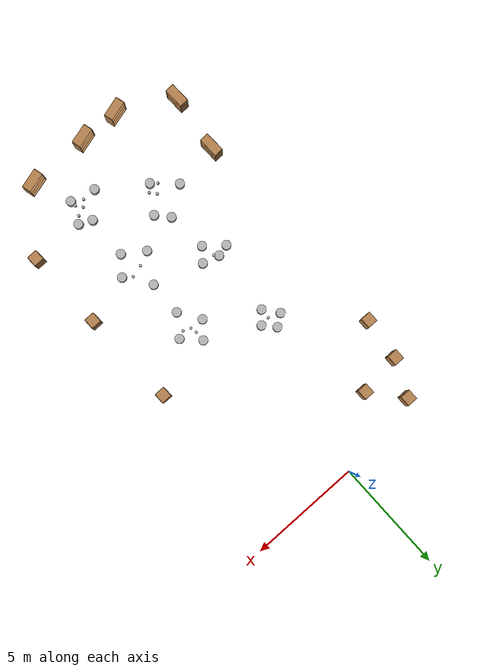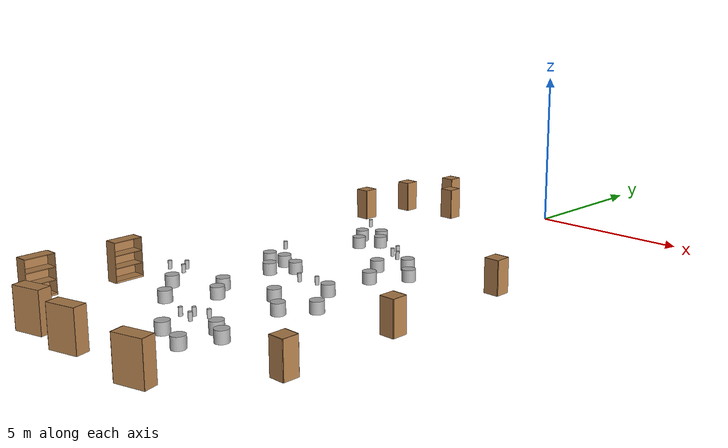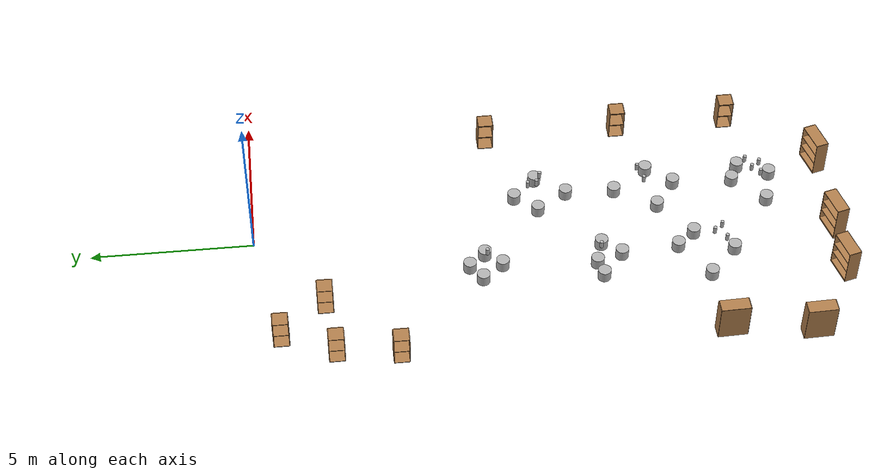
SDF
<sdf version="1.9">
 <world name="world_restaurant">
  <physics name="1ms" type="ignored">
   <max_step_size>0.001</max_step_size>
   <real_time_factor>1</real_time_factor>
   <real_time_update_rate>1000</real_time_update_rate>
  </physics>
  <plugin name="ignition::gazebo::systems::Physics" filename="ignition-gazebo-physics-system"/>
  <plugin name="ignition::gazebo::systems::UserCommands" filename="ignition-gazebo-user-commands-system"/>
  <plugin name="ignition::gazebo::systems::SceneBroadcaster" filename="ignition-gazebo-scene-broadcaster-system"/>
  <plugin name="ignition::gazebo::systems::Contact" filename="ignition-gazebo-contact-system"/>
  <plugin name="ignition::gazebo::systems::Sensors" filename="libignition-gazebo-sensors-system.so">
   <render_engine>ogre2</render_engine>
  </plugin>
  <plugin name="ignition::gazebo::systems::Imu" filename="libignition-gazebo-imu-system.so"/>
  <gravity>0 0 -9.8</gravity>
  <magnetic_field>6e-06 2.3e-05 -4.2e-05</magnetic_field>
  <atmosphere type="adiabatic"/>
  <scene><ambient>0.4 0.4 0.4 1</ambient><background>0.7 0.7 0.7 1</background><shadows>true</shadows></scene>
  <model name="bookshelf">
   <static>true</static>
   <link name="link">
    <inertial>
     <mass>1</mass>
     <inertia><ixx>1</ixx><ixy>0</ixy><ixz>0</ixz><iyy>1</iyy><iyz>0</iyz><izz>1</izz></inertia>
    </inertial>
    <collision name="back">
     <pose>0 0.005 0.6 0 0 0</pose>
     <geometry><box><size>0.9 0.01 1.2</size></box></geometry>
    </collision>
    <visual name="visual1">
     <pose>0 0.005 0.6 0 0 0</pose>
     <geometry><box><size>0.9 0.01 1.2</size></box></geometry>
     <material>
      <script><uri>file://media/materials/scripts/gazebo.material</uri><name>Gazebo/Wood</name></script>
     </material>
    </visual>
    <collision name="left_side">
     <pose>0.45 -0.195 0.6 0 0 0</pose>
     <geometry><box><size>0.02 0.4 1.2</size></box></geometry>
    </collision>
    <visual name="visual2">
     <pose>0.45 -0.195 0.6 0 0 0</pose>
     <geometry><box><size>0.02 0.4 1.2</size></box></geometry>
     <material>
      <script><uri>file://media/materials/scripts/gazebo.material</uri><name>Gazebo/Wood</name></script>
     </material>
    </visual>
    <collision name="right_side">
     <pose>-0.45 -0.195 0.6 0 0 0</pose>
     <geometry><box><size>0.02 0.4 1.2</size></box></geometry>
    </collision>
    <visual name="visual3">
     <pose>-0.45 -0.195 0.6 0 0 0</pose>
     <geometry><box><size>0.02 0.4 1.2</size></box></geometry>
     <material>
      <script><uri>file://media/materials/scripts/gazebo.material</uri><name>Gazebo/Wood</name></script>
     </material>
    </visual>
    <collision name="bottom">
     <pose>0 -0.195 0.03 0 0 0</pose>
     <geometry><box><size>0.88 0.4 0.06</size></box></geometry>
    </collision>
    <visual name="visual4">
     <pose>0 -0.195 0.03 0 0 0</pose>
     <geometry><box><size>0.88 0.4 0.06</size></box></geometry>
     <material>
      <script><uri>file://media/materials/scripts/gazebo.material</uri><name>Gazebo/Wood</name></script>
     </material>
    </visual>
    <collision name="top">
     <pose>0 -0.195 1.19 0 0 0</pose>
     <geometry><box><size>0.88 0.4 0.02</size></box></geometry>
    </collision>
    <visual name="visual5">
     <pose>0 -0.195 1.19 0 0 0</pose>
     <geometry><box><size>0.88 0.4 0.02</size></box></geometry>
     <material>
      <script><uri>file://media/materials/scripts/gazebo.material</uri><name>Gazebo/Wood</name></script>
     </material>
    </visual>
    <collision name="low_shelf">
     <pose>0 -0.195 0.43 0 0 0</pose>
     <geometry><box><size>0.88 0.4 0.02</size></box></geometry>
    </collision>
    <visual name="visual6">
     <pose>0 -0.195 0.43 0 0 0</pose>
     <geometry><box><size>0.88 0.4 0.02</size></box></geometry>
     <material>
      <script><uri>file://media/materials/scripts/gazebo.material</uri><name>Gazebo/Wood</name></script>
     </material>
    </visual>
    <collision name="high_shelf">
     <pose>0 -0.195 0.8 0 0 0</pose>
     <geometry><box><size>0.88 0.4 0.02</size></box></geometry>
    </collision>
    <visual name="visual7">
     <pose>0 -0.195 0.8 0 0 0</pose>
     <geometry><box><size>0.88 0.4 0.02</size></box></geometry>
     <material>
      <script><uri>file://media/materials/scripts/gazebo.material</uri><name>Gazebo/Wood</name></script>
     </material>
    </visual>
   </link>
   <pose>-5 -14 0 0 -0 1.6</pose>
  </model>
  <model name="beer">
   <link name="link">
    <pose>0 0 0.115 0 -0 0</pose>
    <inertial>
     <mass>0.39000000000000001</mass>
     <inertia>
      <ixx>0.00058</ixx>
      <ixy>0</ixy>
      <ixz>0</ixz>
      <iyy>0.00058</iyy>
      <iyz>0</iyz>
      <izz>0.00019000000000000001</izz>
     </inertia>
    </inertial>
    <collision name="collision">
     <geometry><cylinder><radius>0.055</radius><length>0.23000000000000001</length></cylinder></geometry>
    </collision>
    <visual name="visual">
     <geometry><cylinder><radius>0.055</radius><length>0.23000000000000001</length></cylinder></geometry>
     <material>
      <script>
       <uri>file:///home/joan/ros2_ws/install/turtlebot3/share/turtlebot3/models/worlds/model://beer/materials/scripts</uri>
       <uri>model://beer/materials/textures</uri>
       <name>Beer/Diffuse</name>
      </script>
     </material>
    </visual>
   </link>
   <pose>-1.8 -10.5005 0.775 0 0 -7.8e-05</pose>
   <static>false</static>
  </model>
  <model name="cylinder">
   <pose>-1.8 -6.5 0.364799 0 -0 0.0003</pose>
   <link name="cylinder_link">
    <inertial>
     <inertia>
      <ixx>0.14580000000000001</ixx>
      <ixy>0</ixy>
      <ixz>0</ixz>
      <iyy>0.14580000000000001</iyy>
      <iyz>0</iyz>
      <izz>0.125</izz>
     </inertia>
     <mass>1</mass>
    </inertial>
    <collision name="cylinder_collision">
     <geometry>
      <cylinder><radius>0.20000000000000001</radius><length>0.34999999999999998</length></cylinder>
     </geometry>
    </collision>
    <visual name="cylinder_visual">
     <geometry>
      <cylinder><radius>0.20000000000000001</radius><length>0.34999999999999998</length></cylinder>
     </geometry>
     <material>
      <ambient>0.3 0.3 0.3 1</ambient>
      <diffuse>0.7 0.7 0.7 1</diffuse>
      <specular>1 1 1 1</specular>
     </material>
    </visual>
   </link>
   <static>false</static>
  </model>
  <model name="cylinder_1">
   <pose>-1.35 -7 0.364799 0 -0 0.0003</pose>
   <link name="cylinder_link">
    <inertial>
     <inertia>
      <ixx>0.14580000000000001</ixx>
      <ixy>0</ixy>
      <ixz>0</ixz>
      <iyy>0.14580000000000001</iyy>
      <iyz>0</iyz>
      <izz>0.125</izz>
     </inertia>
     <mass>1</mass>
    </inertial>
    <collision name="cylinder_collision">
     <geometry>
      <cylinder><radius>0.20000000000000001</radius><length>0.34999999999999998</length></cylinder>
     </geometry>
    </collision>
    <visual name="cylinder_visual">
     <geometry>
      <cylinder><radius>0.20000000000000001</radius><length>0.34999999999999998</length></cylinder>
     </geometry>
     <material>
      <ambient>0.3 0.3 0.3 1</ambient>
      <diffuse>0.7 0.7 0.7 1</diffuse>
      <specular>1 1 1 1</specular>
     </material>
    </visual>
   </link>
   <static>false</static>
  </model>
  <model name="cylinder_1_1">
   <pose>-1.9971 -10.3842 0.364799 0 -0 0.034565</pose>
   <link name="cylinder_link">
    <inertial>
     <inertia>
      <ixx>0.14580000000000001</ixx>
      <ixy>0</ixy>
      <ixz>0</ixz>
      <iyy>0.14580000000000001</iyy>
      <iyz>0</iyz>
      <izz>0.125</izz>
     </inertia>
     <mass>1</mass>
    </inertial>
    <collision name="cylinder_collision">
     <geometry>
      <cylinder><radius>0.20000000000000001</radius><length>0.34999999999999998</length></cylinder>
     </geometry>
    </collision>
    <visual name="cylinder_visual">
     <geometry>
      <cylinder><radius>0.20000000000000001</radius><length>0.34999999999999998</length></cylinder>
     </geometry>
     <material>
      <ambient>0.3 0.3 0.3 1</ambient>
      <diffuse>0.7 0.7 0.7 1</diffuse>
      <specular>1 1 1 1</specular>
     </material>
    </visual>
   </link>
   <static>false</static>
  </model>
  <model name="cylinder_1_1_1">
   <pose>-1.8 -7.5 0.364799 0 -0 0.0003</pose>
   <link name="cylinder_link">
    <inertial>
     <inertia>
      <ixx>0.14580000000000001</ixx>
      <ixy>0</ixy>
      <ixz>0</ixz>
      <iyy>0.14580000000000001</iyy>
      <iyz>0</iyz>
      <izz>0.125</izz>
     </inertia>
     <mass>1</mass>
    </inertial>
    <collision name="cylinder_collision">
     <geometry>
      <cylinder><radius>0.20000000000000001</radius><length>0.34999999999999998</length></cylinder>
     </geometry>
    </collision>
    <visual name="cylinder_visual">
     <geometry>
      <cylinder><radius>0.20000000000000001</radius><length>0.34999999999999998</length></cylinder>
     </geometry>
     <material>
      <ambient>0.3 0.3 0.3 1</ambient>
      <diffuse>0.7 0.7 0.7 1</diffuse>
      <specular>1 1 1 1</specular>
     </material>
    </visual>
   </link>
   <static>false</static>
  </model>
  <model name="cylinder_1_1_2">
   <pose>-2.3 -6.8583 0.364799 0 -0 0.0003</pose>
   <link name="cylinder_link">
    <inertial>
     <inertia>
      <ixx>0.14580000000000001</ixx>
      <ixy>0</ixy>
      <ixz>0</ixz>
      <iyy>0.14580000000000001</iyy>
      <iyz>0</iyz>
      <izz>0.125</izz>
     </inertia>
     <mass>1</mass>
    </inertial>
    <collision name="cylinder_collision">
     <geometry>
      <cylinder><radius>0.20000000000000001</radius><length>0.34999999999999998</length></cylinder>
     </geometry>
    </collision>
    <visual name="cylinder_visual">
     <geometry>
      <cylinder><radius>0.20000000000000001</radius><length>0.34999999999999998</length></cylinder>
     </geometry>
     <material>
      <ambient>0.3 0.3 0.3 1</ambient>
      <diffuse>0.7 0.7 0.7 1</diffuse>
      <specular>1 1 1 1</specular>
     </material>
    </visual>
   </link>
   <static>false</static>
  </model>
  <model name="beer_1">
   <link name="link">
    <pose>0 0 0.115 0 -0 0</pose>
    <inertial>
     <mass>0.39000000000000001</mass>
     <inertia>
      <ixx>0.00058</ixx>
      <ixy>0</ixy>
      <ixz>0</ixz>
      <iyy>0.00058</iyy>
      <iyz>0</iyz>
      <izz>0.00019000000000000001</izz>
     </inertia>
    </inertial>
    <collision name="collision">
     <geometry><cylinder><radius>0.055</radius><length>0.23000000000000001</length></cylinder></geometry>
    </collision>
    <visual name="visual">
     <geometry><cylinder><radius>0.055</radius><length>0.23000000000000001</length></cylinder></geometry>
     <material>
      <script>
       <uri>file:///home/joan/ros2_ws/install/turtlebot3/share/turtlebot3/models/worlds/model://beer/materials/scripts</uri>
       <uri>model://beer/materials/textures</uri>
       <name>Beer/Diffuse</name>
      </script>
     </material>
    </visual>
   </link>
   <pose>-1.74324 -7.03446 0.775 0 -0 -7.8e-05</pose>
   <static>false</static>
  </model>
  <model name="beer_2">
   <link name="link">
    <pose>0 0 0.115 0 -0 0</pose>
    <inertial>
     <mass>0.39000000000000001</mass>
     <inertia>
      <ixx>0.00058</ixx>
      <ixy>0</ixy>
      <ixz>0</ixz>
      <iyy>0.00058</iyy>
      <iyz>0</iyz>
      <izz>0.00019000000000000001</izz>
     </inertia>
    </inertial>
    <collision name="collision">
     <geometry><cylinder><radius>0.055</radius><length>0.23000000000000001</length></cylinder></geometry>
    </collision>
    <visual name="visual">
     <geometry><cylinder><radius>0.055</radius><length>0.23000000000000001</length></cylinder></geometry>
     <material>
      <script>
       <uri>file:///home/joan/ros2_ws/install/turtlebot3/share/turtlebot3/models/worlds/model://beer/materials/scripts</uri>
       <uri>model://beer/materials/textures</uri>
       <name>Beer/Diffuse</name>
      </script>
     </material>
    </visual>
   </link>
   <pose>0.943448 -8.86355 0.775 0 0 -7.8e-05</pose>
   <static>false</static>
  </model>
  <model name="beer_1_1">
   <link name="link">
    <pose>0 0 0.115 0 -0 0</pose>
    <inertial>
     <mass>0.39000000000000001</mass>
     <inertia>
      <ixx>0.00058</ixx>
      <ixy>0</ixy>
      <ixz>0</ixz>
      <iyy>0.00058</iyy>
      <iyz>0</iyz>
      <izz>0.00019000000000000001</izz>
     </inertia>
    </inertial>
    <collision name="collision">
     <geometry><cylinder><radius>0.055</radius><length>0.23000000000000001</length></cylinder></geometry>
    </collision>
    <visual name="visual">
     <geometry><cylinder><radius>0.055</radius><length>0.23000000000000001</length></cylinder></geometry>
     <material>
      <script>
       <uri>file:///home/joan/ros2_ws/install/turtlebot3/share/turtlebot3/models/worlds/model://beer/materials/scripts</uri>
       <uri>model://beer/materials/textures</uri>
       <name>Beer/Diffuse</name>
      </script>
     </material>
    </visual>
   </link>
   <pose>0.889987 -8.58647 0.775 -0 -0 -7.8e-05</pose>
   <static>false</static>
  </model>
  <model name="beer_1_2">
   <link name="link">
    <pose>0 0 0.115 0 -0 0</pose>
    <inertial>
     <mass>0.39000000000000001</mass>
     <inertia>
      <ixx>0.00058</ixx>
      <ixy>0</ixy>
      <ixz>0</ixz>
      <iyy>0.00058</iyy>
      <iyz>0</iyz>
      <izz>0.00019000000000000001</izz>
     </inertia>
    </inertial>
    <collision name="collision">
     <geometry><cylinder><radius>0.055</radius><length>0.23000000000000001</length></cylinder></geometry>
    </collision>
    <visual name="visual">
     <geometry><cylinder><radius>0.055</radius><length>0.23000000000000001</length></cylinder></geometry>
     <material>
      <script>
       <uri>file:///home/joan/ros2_ws/install/turtlebot3/share/turtlebot3/models/worlds/model://beer/materials/scripts</uri>
       <uri>model://beer/materials/textures</uri>
       <name>Beer/Diffuse</name>
      </script>
     </material>
    </visual>
   </link>
   <pose>1.26044 -8.99729 0.775 0 0 -7.8e-05</pose>
   <static>false</static>
  </model>
  <model name="beer_1_3">
   <link name="link">
    <pose>0 0 0.115 0 -0 0</pose>
    <inertial>
     <mass>0.39000000000000001</mass>
     <inertia>
      <ixx>0.00058</ixx>
      <ixy>0</ixy>
      <ixz>0</ixz>
      <iyy>0.00058</iyy>
      <iyz>0</iyz>
      <izz>0.00019000000000000001</izz>
     </inertia>
    </inertial>
    <collision name="collision">
     <geometry><cylinder><radius>0.055</radius><length>0.23000000000000001</length></cylinder></geometry>
    </collision>
    <visual name="visual">
     <geometry><cylinder><radius>0.055</radius><length>0.23000000000000001</length></cylinder></geometry>
     <material>
      <script>
       <uri>file:///home/joan/ros2_ws/install/turtlebot3/share/turtlebot3/models/worlds/model://beer/materials/scripts</uri>
       <uri>model://beer/materials/textures</uri>
       <name>Beer/Diffuse</name>
      </script>
     </material>
    </visual>
   </link>
   <pose>0.76975 -12.2189 0.775 0 0 -7.8e-05</pose>
   <static>false</static>
  </model>
  <model name="beer_1_4">
   <link name="link">
    <pose>0 0 0.115 0 -0 0</pose>
    <inertial>
     <mass>0.39000000000000001</mass>
     <inertia>
      <ixx>0.00058</ixx>
      <ixy>0</ixy>
      <ixz>0</ixz>
      <iyy>0.00058</iyy>
      <iyz>0</iyz>
      <izz>0.00019000000000000001</izz>
     </inertia>
    </inertial>
    <collision name="collision">
     <geometry><cylinder><radius>0.055</radius><length>0.23000000000000001</length></cylinder></geometry>
    </collision>
    <visual name="visual">
     <geometry><cylinder><radius>0.055</radius><length>0.23000000000000001</length></cylinder></geometry>
     <material>
      <script>
       <uri>file:///home/joan/ros2_ws/install/turtlebot3/share/turtlebot3/models/worlds/model://beer/materials/scripts</uri>
       <uri>model://beer/materials/textures</uri>
       <name>Beer/Diffuse</name>
      </script>
     </material>
    </visual>
   </link>
   <pose>1.29815 -12.0805 0.775 0 0 -7.8e-05</pose>
   <static>false</static>
  </model>
  <model name="cylinder_1_2">
   <pose>0.886542 -8.16521 0.364799 0 -0 0.0003</pose>
   <link name="cylinder_link">
    <inertial>
     <inertia>
      <ixx>0.14580000000000001</ixx>
      <ixy>0</ixy>
      <ixz>0</ixz>
      <iyy>0.14580000000000001</iyy>
      <iyz>0</iyz>
      <izz>0.125</izz>
     </inertia>
     <mass>1</mass>
    </inertial>
    <collision name="cylinder_collision">
     <geometry>
      <cylinder><radius>0.20000000000000001</radius><length>0.34999999999999998</length></cylinder>
     </geometry>
    </collision>
    <visual name="cylinder_visual">
     <geometry>
      <cylinder><radius>0.20000000000000001</radius><length>0.34999999999999998</length></cylinder>
     </geometry>
     <material>
      <ambient>0.3 0.3 0.3 1</ambient>
      <diffuse>0.7 0.7 0.7 1</diffuse>
      <specular>1 1 1 1</specular>
     </material>
    </visual>
   </link>
   <static>false</static>
  </model>
  <model name="cylinder_1_3">
   <pose>0.32062 -8.84854 0.364799 0 -0 0.0003</pose>
   <link name="cylinder_link">
    <inertial>
     <inertia>
      <ixx>0.14580000000000001</ixx>
      <ixy>0</ixy>
      <ixz>0</ixz>
      <iyy>0.14580000000000001</iyy>
      <iyz>0</iyz>
      <izz>0.125</izz>
     </inertia>
     <mass>1</mass>
    </inertial>
    <collision name="cylinder_collision">
     <geometry>
      <cylinder><radius>0.20000000000000001</radius><length>0.34999999999999998</length></cylinder>
     </geometry>
    </collision>
    <visual name="cylinder_visual">
     <geometry>
      <cylinder><radius>0.20000000000000001</radius><length>0.34999999999999998</length></cylinder>
     </geometry>
     <material>
      <ambient>0.3 0.3 0.3 1</ambient>
      <diffuse>0.7 0.7 0.7 1</diffuse>
      <specular>1 1 1 1</specular>
     </material>
    </visual>
   </link>
   <static>false</static>
  </model>
  <model name="cylinder_1_4">
   <pose>0.933209 -9.78972 0.364799 0 -0 0.0003</pose>
   <link name="cylinder_link">
    <inertial>
     <inertia>
      <ixx>0.14580000000000001</ixx>
      <ixy>0</ixy>
      <ixz>0</ixz>
      <iyy>0.14580000000000001</iyy>
      <iyz>0</iyz>
      <izz>0.125</izz>
     </inertia>
     <mass>1</mass>
    </inertial>
    <collision name="cylinder_collision">
     <geometry>
      <cylinder><radius>0.20000000000000001</radius><length>0.34999999999999998</length></cylinder>
     </geometry>
    </collision>
    <visual name="cylinder_visual">
     <geometry>
      <cylinder><radius>0.20000000000000001</radius><length>0.34999999999999998</length></cylinder>
     </geometry>
     <material>
      <ambient>0.3 0.3 0.3 1</ambient>
      <diffuse>0.7 0.7 0.7 1</diffuse>
      <specular>1 1 1 1</specular>
     </material>
    </visual>
   </link>
   <static>false</static>
  </model>
  <model name="cylinder_1_5">
   <pose>1.58796 -8.87831 0.364799 0 -0 0.0003</pose>
   <link name="cylinder_link">
    <inertial>
     <inertia>
      <ixx>0.14580000000000001</ixx>
      <ixy>0</ixy>
      <ixz>0</ixz>
      <iyy>0.14580000000000001</iyy>
      <iyz>0</iyz>
      <izz>0.125</izz>
     </inertia>
     <mass>1</mass>
    </inertial>
    <collision name="cylinder_collision">
     <geometry>
      <cylinder><radius>0.20000000000000001</radius><length>0.34999999999999998</length></cylinder>
     </geometry>
    </collision>
    <visual name="cylinder_visual">
     <geometry>
      <cylinder><radius>0.20000000000000001</radius><length>0.34999999999999998</length></cylinder>
     </geometry>
     <material>
      <ambient>0.3 0.3 0.3 1</ambient>
      <diffuse>0.7 0.7 0.7 1</diffuse>
      <specular>1 1 1 1</specular>
     </material>
    </visual>
   </link>
   <static>false</static>
  </model>
  <model name="cylinder_1_6">
   <pose>0.877834 -11.3115 0.364799 0 -0 0.0003</pose>
   <link name="cylinder_link">
    <inertial>
     <inertia>
      <ixx>0.14580000000000001</ixx>
      <ixy>0</ixy>
      <ixz>0</ixz>
      <iyy>0.14580000000000001</iyy>
      <iyz>0</iyz>
      <izz>0.125</izz>
     </inertia>
     <mass>1</mass>
    </inertial>
    <collision name="cylinder_collision">
     <geometry>
      <cylinder><radius>0.20000000000000001</radius><length>0.34999999999999998</length></cylinder>
     </geometry>
    </collision>
    <visual name="cylinder_visual">
     <geometry>
      <cylinder><radius>0.20000000000000001</radius><length>0.34999999999999998</length></cylinder>
     </geometry>
     <material>
      <ambient>0.3 0.3 0.3 1</ambient>
      <diffuse>0.7 0.7 0.7 1</diffuse>
      <specular>1 1 1 1</specular>
     </material>
    </visual>
   </link>
   <static>false</static>
  </model>
  <model name="cylinder_1_7">
   <pose>0.131344 -12.5614 0.364799 0 -0 0.0003</pose>
   <link name="cylinder_link">
    <inertial>
     <inertia>
      <ixx>0.14580000000000001</ixx>
      <ixy>0</ixy>
      <ixz>0</ixz>
      <iyy>0.14580000000000001</iyy>
      <iyz>0</iyz>
      <izz>0.125</izz>
     </inertia>
     <mass>1</mass>
    </inertial>
    <collision name="cylinder_collision">
     <geometry>
      <cylinder><radius>0.20000000000000001</radius><length>0.34999999999999998</length></cylinder>
     </geometry>
    </collision>
    <visual name="cylinder_visual">
     <geometry>
      <cylinder><radius>0.20000000000000001</radius><length>0.34999999999999998</length></cylinder>
     </geometry>
     <material>
      <ambient>0.3 0.3 0.3 1</ambient>
      <diffuse>0.7 0.7 0.7 1</diffuse>
      <specular>1 1 1 1</specular>
     </material>
    </visual>
   </link>
   <static>false</static>
  </model>
  <model name="cylinder_1_8">
   <pose>1.66853 -12.4257 0.364799 0 -0 0.0003</pose>
   <link name="cylinder_link">
    <inertial>
     <inertia>
      <ixx>0.14580000000000001</ixx>
      <ixy>0</ixy>
      <ixz>0</ixz>
      <iyy>0.14580000000000001</iyy>
      <iyz>0</iyz>
      <izz>0.125</izz>
     </inertia>
     <mass>1</mass>
    </inertial>
    <collision name="cylinder_collision">
     <geometry>
      <cylinder><radius>0.20000000000000001</radius><length>0.34999999999999998</length></cylinder>
     </geometry>
    </collision>
    <visual name="cylinder_visual">
     <geometry>
      <cylinder><radius>0.20000000000000001</radius><length>0.34999999999999998</length></cylinder>
     </geometry>
     <material>
      <ambient>0.3 0.3 0.3 1</ambient>
      <diffuse>0.7 0.7 0.7 1</diffuse>
      <specular>1 1 1 1</specular>
     </material>
    </visual>
   </link>
   <static>false</static>
  </model>
  <model name="cylinder_1_9">
   <pose>1.04747 -13.2016 0.364799 0 -0 0.0003</pose>
   <link name="cylinder_link">
    <inertial>
     <inertia>
      <ixx>0.14580000000000001</ixx>
      <ixy>0</ixy>
      <ixz>0</ixz>
      <iyy>0.14580000000000001</iyy>
      <iyz>0</iyz>
      <izz>0.125</izz>
     </inertia>
     <mass>1</mass>
    </inertial>
    <collision name="cylinder_collision">
     <geometry>
      <cylinder><radius>0.20000000000000001</radius><length>0.34999999999999998</length></cylinder>
     </geometry>
    </collision>
    <visual name="cylinder_visual">
     <geometry>
      <cylinder><radius>0.20000000000000001</radius><length>0.34999999999999998</length></cylinder>
     </geometry>
     <material>
      <ambient>0.3 0.3 0.3 1</ambient>
      <diffuse>0.7 0.7 0.7 1</diffuse>
      <specular>1 1 1 1</specular>
     </material>
    </visual>
   </link>
   <static>false</static>
  </model>
  <model name="cylinder_1_10">
   <pose>0.974089 -15.0716 0.364799 0 0 -0.005798</pose>
   <link name="cylinder_link">
    <inertial>
     <inertia>
      <ixx>0.14580000000000001</ixx>
      <ixy>0</ixy>
      <ixz>0</ixz>
      <iyy>0.14580000000000001</iyy>
      <iyz>0</iyz>
      <izz>0.125</izz>
     </inertia>
     <mass>1</mass>
    </inertial>
    <collision name="cylinder_collision">
     <geometry>
      <cylinder><radius>0.20000000000000001</radius><length>0.34999999999999998</length></cylinder>
     </geometry>
    </collision>
    <visual name="cylinder_visual">
     <geometry>
      <cylinder><radius>0.20000000000000001</radius><length>0.34999999999999998</length></cylinder>
     </geometry>
     <material>
      <ambient>0.3 0.3 0.3 1</ambient>
      <diffuse>0.7 0.7 0.7 1</diffuse>
      <specular>1 1 1 1</specular>
     </material>
    </visual>
   </link>
   <static>false</static>
  </model>
  <model name="cylinder_1_11">
   <pose>1.13113 -16.2878 0.364799 0 -0 0.0003</pose>
   <link name="cylinder_link">
    <inertial>
     <inertia>
      <ixx>0.14580000000000001</ixx>
      <ixy>0</ixy>
      <ixz>0</ixz>
      <iyy>0.14580000000000001</iyy>
      <iyz>0</iyz>
      <izz>0.125</izz>
     </inertia>
     <mass>1</mass>
    </inertial>
    <collision name="cylinder_collision">
     <geometry>
      <cylinder><radius>0.20000000000000001</radius><length>0.34999999999999998</length></cylinder>
     </geometry>
    </collision>
    <visual name="cylinder_visual">
     <geometry>
      <cylinder><radius>0.20000000000000001</radius><length>0.34999999999999998</length></cylinder>
     </geometry>
     <material>
      <ambient>0.3 0.3 0.3 1</ambient>
      <diffuse>0.7 0.7 0.7 1</diffuse>
      <specular>1 1 1 1</specular>
     </material>
    </visual>
   </link>
   <static>false</static>
  </model>
  <model name="cylinder_1_12">
   <pose>0.05 -16 0.364799 0 -0 0</pose>
   <link name="cylinder_link">
    <inertial>
     <inertia>
      <ixx>0.14580000000000001</ixx>
      <ixy>0</ixy>
      <ixz>0</ixz>
      <iyy>0.14580000000000001</iyy>
      <iyz>0</iyz>
      <izz>0.125</izz>
     </inertia>
     <mass>1</mass>
    </inertial>
    <collision name="cylinder_collision">
     <geometry>
      <cylinder><radius>0.20000000000000001</radius><length>0.34999999999999998</length></cylinder>
     </geometry>
    </collision>
    <visual name="cylinder_visual">
     <geometry>
      <cylinder><radius>0.20000000000000001</radius><length>0.34999999999999998</length></cylinder>
     </geometry>
     <material>
      <ambient>0.3 0.3 0.3 1</ambient>
      <diffuse>0.7 0.7 0.7 1</diffuse>
      <specular>1 1 1 1</specular>
     </material>
    </visual>
   </link>
   <static>false</static>
  </model>
  <model name="cylinder_1_13">
   <pose>1.53352 -15.3395 0.364799 0 -0 0.0003</pose>
   <link name="cylinder_link">
    <inertial>
     <inertia>
      <ixx>0.14580000000000001</ixx>
      <ixy>0</ixy>
      <ixz>0</ixz>
      <iyy>0.14580000000000001</iyy>
      <iyz>0</iyz>
      <izz>0.125</izz>
     </inertia>
     <mass>1</mass>
    </inertial>
    <collision name="cylinder_collision">
     <geometry>
      <cylinder><radius>0.20000000000000001</radius><length>0.34999999999999998</length></cylinder>
     </geometry>
    </collision>
    <visual name="cylinder_visual">
     <geometry>
      <cylinder><radius>0.20000000000000001</radius><length>0.34999999999999998</length></cylinder>
     </geometry>
     <material>
      <ambient>0.3 0.3 0.3 1</ambient>
      <diffuse>0.7 0.7 0.7 1</diffuse>
      <specular>1 1 1 1</specular>
     </material>
    </visual>
   </link>
   <static>false</static>
  </model>
  <model name="cylinder_1_14">
   <pose>-1.26283 -10.602 0.364799 0 -0 0.0003</pose>
   <link name="cylinder_link">
    <inertial>
     <inertia>
      <ixx>0.14580000000000001</ixx>
      <ixy>0</ixy>
      <ixz>0</ixz>
      <iyy>0.14580000000000001</iyy>
      <iyz>0</iyz>
      <izz>0.125</izz>
     </inertia>
     <mass>1</mass>
    </inertial>
    <collision name="cylinder_collision">
     <geometry>
      <cylinder><radius>0.20000000000000001</radius><length>0.34999999999999998</length></cylinder>
     </geometry>
    </collision>
    <visual name="cylinder_visual">
     <geometry>
      <cylinder><radius>0.20000000000000001</radius><length>0.34999999999999998</length></cylinder>
     </geometry>
     <material>
      <ambient>0.3 0.3 0.3 1</ambient>
      <diffuse>0.7 0.7 0.7 1</diffuse>
      <specular>1 1 1 1</specular>
     </material>
    </visual>
   </link>
   <static>false</static>
  </model>
  <model name="cylinder_1_15">
   <pose>-1.72796 -11.1717 0.364799 0 -0 0.0003</pose>
   <link name="cylinder_link">
    <inertial>
     <inertia>
      <ixx>0.14580000000000001</ixx>
      <ixy>0</ixy>
      <ixz>0</ixz>
      <iyy>0.14580000000000001</iyy>
      <iyz>0</iyz>
      <izz>0.125</izz>
     </inertia>
     <mass>1</mass>
    </inertial>
    <collision name="cylinder_collision">
     <geometry>
      <cylinder><radius>0.20000000000000001</radius><length>0.34999999999999998</length></cylinder>
     </geometry>
    </collision>
    <visual name="cylinder_visual">
     <geometry>
      <cylinder><radius>0.20000000000000001</radius><length>0.34999999999999998</length></cylinder>
     </geometry>
     <material>
      <ambient>0.3 0.3 0.3 1</ambient>
      <diffuse>0.7 0.7 0.7 1</diffuse>
      <specular>1 1 1 1</specular>
     </material>
    </visual>
   </link>
   <static>false</static>
  </model>
  <model name="cylinder_1_16">
   <pose>-2.51816 -10.5117 0.364799 0 -0 0.0003</pose>
   <link name="cylinder_link">
    <inertial>
     <inertia>
      <ixx>0.14580000000000001</ixx>
      <ixy>0</ixy>
      <ixz>0</ixz>
      <iyy>0.14580000000000001</iyy>
      <iyz>0</iyz>
      <izz>0.125</izz>
     </inertia>
     <mass>1</mass>
    </inertial>
    <collision name="cylinder_collision">
     <geometry>
      <cylinder><radius>0.20000000000000001</radius><length>0.34999999999999998</length></cylinder>
     </geometry>
    </collision>
    <visual name="cylinder_visual">
     <geometry>
      <cylinder><radius>0.20000000000000001</radius><length>0.34999999999999998</length></cylinder>
     </geometry>
     <material>
      <ambient>0.3 0.3 0.3 1</ambient>
      <diffuse>0.7 0.7 0.7 1</diffuse>
      <specular>1 1 1 1</specular>
     </material>
    </visual>
   </link>
   <static>false</static>
  </model>
  <model name="cylinder_1_17">
   <pose>-1.58699 -12.9405 0.364799 0 -0 0.0003</pose>
   <link name="cylinder_link">
    <inertial>
     <inertia>
      <ixx>0.14580000000000001</ixx>
      <ixy>0</ixy>
      <ixz>0</ixz>
      <iyy>0.14580000000000001</iyy>
      <iyz>0</iyz>
      <izz>0.125</izz>
     </inertia>
     <mass>1</mass>
    </inertial>
    <collision name="cylinder_collision">
     <geometry>
      <cylinder><radius>0.20000000000000001</radius><length>0.34999999999999998</length></cylinder>
     </geometry>
    </collision>
    <visual name="cylinder_visual">
     <geometry>
      <cylinder><radius>0.20000000000000001</radius><length>0.34999999999999998</length></cylinder>
     </geometry>
     <material>
      <ambient>0.3 0.3 0.3 1</ambient>
      <diffuse>0.7 0.7 0.7 1</diffuse>
      <specular>1 1 1 1</specular>
     </material>
    </visual>
   </link>
   <static>false</static>
  </model>
  <model name="cylinder_1_18">
   <pose>-1.86176 -14.6326 0.364799 0 -0 0.0003</pose>
   <link name="cylinder_link">
    <inertial>
     <inertia>
      <ixx>0.14580000000000001</ixx>
      <ixy>0</ixy>
      <ixz>0</ixz>
      <iyy>0.14580000000000001</iyy>
      <iyz>0</iyz>
      <izz>0.125</izz>
     </inertia>
     <mass>1</mass>
    </inertial>
    <collision name="cylinder_collision">
     <geometry>
      <cylinder><radius>0.20000000000000001</radius><length>0.34999999999999998</length></cylinder>
     </geometry>
    </collision>
    <visual name="cylinder_visual">
     <geometry>
      <cylinder><radius>0.20000000000000001</radius><length>0.34999999999999998</length></cylinder>
     </geometry>
     <material>
      <ambient>0.3 0.3 0.3 1</ambient>
      <diffuse>0.7 0.7 0.7 1</diffuse>
      <specular>1 1 1 1</specular>
     </material>
    </visual>
   </link>
   <static>false</static>
  </model>
  <model name="cylinder_1_19">
   <pose>-2.8 -13.7663 0.364799 0 -0 0</pose>
   <link name="cylinder_link">
    <inertial>
     <inertia>
      <ixx>0.14580000000000001</ixx>
      <ixy>0</ixy>
      <ixz>0</ixz>
      <iyy>0.14580000000000001</iyy>
      <iyz>0</iyz>
      <izz>0.125</izz>
     </inertia>
     <mass>1</mass>
    </inertial>
    <collision name="cylinder_collision">
     <geometry>
      <cylinder><radius>0.20000000000000001</radius><length>0.34999999999999998</length></cylinder>
     </geometry>
    </collision>
    <visual name="cylinder_visual">
     <geometry>
      <cylinder><radius>0.20000000000000001</radius><length>0.34999999999999998</length></cylinder>
     </geometry>
     <material>
      <ambient>0.3 0.3 0.3 1</ambient>
      <diffuse>0.7 0.7 0.7 1</diffuse>
      <specular>1 1 1 1</specular>
     </material>
    </visual>
   </link>
   <static>false</static>
  </model>
  <model name="cylinder_1_20">
   <pose>-1.09581 -13.498 0.364799 0 -0 0.0003</pose>
   <link name="cylinder_link">
    <inertial>
     <inertia>
      <ixx>0.14580000000000001</ixx>
      <ixy>0</ixy>
      <ixz>0</ixz>
      <iyy>0.14580000000000001</iyy>
      <iyz>0</iyz>
      <izz>0.125</izz>
     </inertia>
     <mass>1</mass>
    </inertial>
    <collision name="cylinder_collision">
     <geometry>
      <cylinder><radius>0.20000000000000001</radius><length>0.34999999999999998</length></cylinder>
     </geometry>
    </collision>
    <visual name="cylinder_visual">
     <geometry>
      <cylinder><radius>0.20000000000000001</radius><length>0.34999999999999998</length></cylinder>
     </geometry>
     <material>
      <ambient>0.3 0.3 0.3 1</ambient>
      <diffuse>0.7 0.7 0.7 1</diffuse>
      <specular>1 1 1 1</specular>
     </material>
    </visual>
   </link>
   <static>false</static>
  </model>
  <model name="beer_1_3_1">
   <link name="link">
    <pose>0 0 0.115 0 -0 0</pose>
    <inertial>
     <mass>0.39000000000000001</mass>
     <inertia>
      <ixx>0.00058</ixx>
      <ixy>0</ixy>
      <ixz>0</ixz>
      <iyy>0.00058</iyy>
      <iyz>0</iyz>
      <izz>0.00019000000000000001</izz>
     </inertia>
    </inertial>
    <collision name="collision">
     <geometry><cylinder><radius>0.055</radius><length>0.23000000000000001</length></cylinder></geometry>
    </collision>
    <visual name="visual">
     <geometry><cylinder><radius>0.055</radius><length>0.23000000000000001</length></cylinder></geometry>
     <material>
      <script>
       <uri>file:///home/joan/ros2_ws/install/turtlebot3/share/turtlebot3/models/worlds/model://beer/materials/scripts</uri>
       <uri>model://beer/materials/textures</uri>
       <name>Beer/Diffuse</name>
      </script>
     </material>
    </visual>
   </link>
   <pose>0.917031 -15.6624 0.775 0 0 -7.8e-05</pose>
   <static>false</static>
  </model>
  <model name="beer_1_3_2">
   <link name="link">
    <pose>0 0 0.115 0 -0 0</pose>
    <inertial>
     <mass>0.39000000000000001</mass>
     <inertia>
      <ixx>0.00058</ixx>
      <ixy>0</ixy>
      <ixz>0</ixz>
      <iyy>0.00058</iyy>
      <iyz>0</iyz>
      <izz>0.00019000000000000001</izz>
     </inertia>
    </inertial>
    <collision name="collision">
     <geometry><cylinder><radius>0.055</radius><length>0.23000000000000001</length></cylinder></geometry>
    </collision>
    <visual name="visual">
     <geometry><cylinder><radius>0.055</radius><length>0.23000000000000001</length></cylinder></geometry>
     <material>
      <script>
       <uri>file:///home/joan/ros2_ws/install/turtlebot3/share/turtlebot3/models/worlds/model://beer/materials/scripts</uri>
       <uri>model://beer/materials/textures</uri>
       <name>Beer/Diffuse</name>
      </script>
     </material>
    </visual>
   </link>
   <pose>1.29635 -15.5056 0.775 0 0 -7.8e-05</pose>
   <static>false</static>
  </model>
  <model name="beer_1_3_3">
   <link name="link">
    <pose>0 0 0.115 0 -0 0</pose>
    <inertial>
     <mass>0.39000000000000001</mass>
     <inertia>
      <ixx>0.00058</ixx>
      <ixy>0</ixy>
      <ixz>0</ixz>
      <iyy>0.00058</iyy>
      <iyz>0</iyz>
      <izz>0.00019000000000000001</izz>
     </inertia>
    </inertial>
    <collision name="collision">
     <geometry><cylinder><radius>0.055</radius><length>0.23000000000000001</length></cylinder></geometry>
    </collision>
    <visual name="visual">
     <geometry><cylinder><radius>0.055</radius><length>0.23000000000000001</length></cylinder></geometry>
     <material>
      <script>
       <uri>file:///home/joan/ros2_ws/install/turtlebot3/share/turtlebot3/models/worlds/model://beer/materials/scripts</uri>
       <uri>model://beer/materials/textures</uri>
       <name>Beer/Diffuse</name>
      </script>
     </material>
    </visual>
   </link>
   <pose>1.12425 -15.9241 0.775 0 0 -7.8e-05</pose>
   <static>false</static>
  </model>
  <model name="beer_1_3_4">
   <link name="link">
    <pose>0 0 0.115 0 -0 0</pose>
    <inertial>
     <mass>0.39000000000000001</mass>
     <inertia>
      <ixx>0.00058</ixx>
      <ixy>0</ixy>
      <ixz>0</ixz>
      <iyy>0.00058</iyy>
      <iyz>0</iyz>
      <izz>0.00019000000000000001</izz>
     </inertia>
    </inertial>
    <collision name="collision">
     <geometry><cylinder><radius>0.055</radius><length>0.23000000000000001</length></cylinder></geometry>
    </collision>
    <visual name="visual">
     <geometry><cylinder><radius>0.055</radius><length>0.23000000000000001</length></cylinder></geometry>
     <material>
      <script>
       <uri>file:///home/joan/ros2_ws/install/turtlebot3/share/turtlebot3/models/worlds/model://beer/materials/scripts</uri>
       <uri>model://beer/materials/textures</uri>
       <name>Beer/Diffuse</name>
      </script>
     </material>
    </visual>
   </link>
   <pose>0.688256 -15.8935 0.775 0 0 -7.8e-05</pose>
   <static>false</static>
  </model>
  <model name="beer_1_3_5">
   <link name="link">
    <pose>0 0 0.115 0 -0 0</pose>
    <inertial>
     <mass>0.39000000000000001</mass>
     <inertia>
      <ixx>0.00058</ixx>
      <ixy>0</ixy>
      <ixz>0</ixz>
      <iyy>0.00058</iyy>
      <iyz>0</iyz>
      <izz>0.00019000000000000001</izz>
     </inertia>
    </inertial>
    <collision name="collision">
     <geometry><cylinder><radius>0.055</radius><length>0.23000000000000001</length></cylinder></geometry>
    </collision>
    <visual name="visual">
     <geometry><cylinder><radius>0.055</radius><length>0.23000000000000001</length></cylinder></geometry>
     <material>
      <script>
       <uri>file:///home/joan/ros2_ws/install/turtlebot3/share/turtlebot3/models/worlds/model://beer/materials/scripts</uri>
       <uri>model://beer/materials/textures</uri>
       <name>Beer/Diffuse</name>
      </script>
     </material>
    </visual>
   </link>
   <pose>-1.7523 -13.975 0.975 0 -0 -0.0001</pose>
   <static>false</static>
  </model>
  <model name="beer_1_3_5_1">
   <link name="link">
    <pose>0 0 0.115 0 -0 0</pose>
    <inertial>
     <mass>0.39000000000000001</mass>
     <inertia>
      <ixx>0.00058</ixx>
      <ixy>0</ixy>
      <ixz>0</ixz>
      <iyy>0.00058</iyy>
      <iyz>0</iyz>
      <izz>0.00019000000000000001</izz>
     </inertia>
    </inertial>
    <collision name="collision">
     <geometry><cylinder><radius>0.055</radius><length>0.23000000000000001</length></cylinder></geometry>
    </collision>
    <visual name="visual">
     <geometry><cylinder><radius>0.055</radius><length>0.23000000000000001</length></cylinder></geometry>
     <material>
      <script>
       <uri>file:///home/joan/ros2_ws/install/turtlebot3/share/turtlebot3/models/worlds/model://beer/materials/scripts</uri>
       <uri>model://beer/materials/textures</uri>
       <name>Beer/Diffuse</name>
      </script>
     </material>
    </visual>
   </link>
   <pose>-2.07353 -14.2924 0.975 0 -0 -0.0001</pose>
   <static>false</static>
  </model>
  <model name="beer_1_3_5_2">
   <link name="link">
    <pose>0 0 0.115 0 -0 0</pose>
    <inertial>
     <mass>0.39000000000000001</mass>
     <inertia>
      <ixx>0.00058</ixx>
      <ixy>0</ixy>
      <ixz>0</ixz>
      <iyy>0.00058</iyy>
      <iyz>0</iyz>
      <izz>0.00019000000000000001</izz>
     </inertia>
    </inertial>
    <collision name="collision">
     <geometry><cylinder><radius>0.055</radius><length>0.23000000000000001</length></cylinder></geometry>
    </collision>
    <visual name="visual">
     <geometry><cylinder><radius>0.055</radius><length>0.23000000000000001</length></cylinder></geometry>
     <material>
      <script>
       <uri>file:///home/joan/ros2_ws/install/turtlebot3/share/turtlebot3/models/worlds/model://beer/materials/scripts</uri>
       <uri>model://beer/materials/textures</uri>
       <name>Beer/Diffuse</name>
      </script>
     </material>
    </visual>
   </link>
   <pose>-1.53708 -14.2355 0.975 -0 -0 -0.0001</pose>
   <static>false</static>
  </model>
  <model name="bookshelf_1">
   <static>true</static>
   <link name="link">
    <inertial>
     <mass>1</mass>
     <inertia><ixx>1</ixx><ixy>0</ixy><ixz>0</ixz><iyy>1</iyy><iyz>0</iyz><izz>1</izz></inertia>
    </inertial>
    <collision name="back">
     <pose>0 0.005 0.6 0 0 0</pose>
     <geometry><box><size>0.9 0.01 1.2</size></box></geometry>
    </collision>
    <visual name="visual1">
     <pose>0 0.005 0.6 0 0 0</pose>
     <geometry><box><size>0.9 0.01 1.2</size></box></geometry>
     <material>
      <script><uri>file://media/materials/scripts/gazebo.material</uri><name>Gazebo/Wood</name></script>
     </material>
    </visual>
    <collision name="left_side">
     <pose>0.45 -0.195 0.6 0 0 0</pose>
     <geometry><box><size>0.02 0.4 1.2</size></box></geometry>
    </collision>
    <visual name="visual2">
     <pose>0.45 -0.195 0.6 0 0 0</pose>
     <geometry><box><size>0.02 0.4 1.2</size></box></geometry>
     <material>
      <script><uri>file://media/materials/scripts/gazebo.material</uri><name>Gazebo/Wood</name></script>
     </material>
    </visual>
    <collision name="right_side">
     <pose>-0.45 -0.195 0.6 0 0 0</pose>
     <geometry><box><size>0.02 0.4 1.2</size></box></geometry>
    </collision>
    <visual name="visual3">
     <pose>-0.45 -0.195 0.6 0 0 0</pose>
     <geometry><box><size>0.02 0.4 1.2</size></box></geometry>
     <material>
      <script><uri>file://media/materials/scripts/gazebo.material</uri><name>Gazebo/Wood</name></script>
     </material>
    </visual>
    <collision name="bottom">
     <pose>0 -0.195 0.03 0 0 0</pose>
     <geometry><box><size>0.88 0.4 0.06</size></box></geometry>
    </collision>
    <visual name="visual4">
     <pose>0 -0.195 0.03 0 0 0</pose>
     <geometry><box><size>0.88 0.4 0.06</size></box></geometry>
     <material>
      <script><uri>file://media/materials/scripts/gazebo.material</uri><name>Gazebo/Wood</name></script>
     </material>
    </visual>
    <collision name="top">
     <pose>0 -0.195 1.19 0 0 0</pose>
     <geometry><box><size>0.88 0.4 0.02</size></box></geometry>
    </collision>
    <visual name="visual5">
     <pose>0 -0.195 1.19 0 0 0</pose>
     <geometry><box><size>0.88 0.4 0.02</size></box></geometry>
     <material>
      <script><uri>file://media/materials/scripts/gazebo.material</uri><name>Gazebo/Wood</name></script>
     </material>
    </visual>
    <collision name="low_shelf">
     <pose>0 -0.195 0.43 0 0 0</pose>
     <geometry><box><size>0.88 0.4 0.02</size></box></geometry>
    </collision>
    <visual name="visual6">
     <pose>0 -0.195 0.43 0 0 0</pose>
     <geometry><box><size>0.88 0.4 0.02</size></box></geometry>
     <material>
      <script><uri>file://media/materials/scripts/gazebo.material</uri><name>Gazebo/Wood</name></script>
     </material>
    </visual>
    <collision name="high_shelf">
     <pose>0 -0.195 0.8 0 0 0</pose>
     <geometry><box><size>0.88 0.4 0.02</size></box></geometry>
    </collision>
    <visual name="visual7">
     <pose>0 -0.195 0.8 0 0 0</pose>
     <geometry><box><size>0.88 0.4 0.02</size></box></geometry>
     <material>
      <script><uri>file://media/materials/scripts/gazebo.material</uri><name>Gazebo/Wood</name></script>
     </material>
    </visual>
   </link>
   <pose>-5.31585 -16.5315 0 0 -0 1.6</pose>
  </model>
  <model name="bookshelf_3_1">
   <static>true</static>
   <link name="link">
    <inertial>
     <mass>1</mass>
     <inertia><ixx>1</ixx><ixy>0</ixy><ixz>0</ixz><iyy>1</iyy><iyz>0</iyz><izz>1</izz></inertia>
    </inertial>
    <collision name="back">
     <pose>0 0.005 0.6 0 0 0</pose>
     <geometry><box><size>0.9 0.01 1.2</size></box></geometry>
    </collision>
    <visual name="visual1">
     <pose>0 0.005 0.6 0 0 0</pose>
     <geometry><box><size>0.9 0.01 1.2</size></box></geometry>
     <material>
      <script><uri>file://media/materials/scripts/gazebo.material</uri><name>Gazebo/Wood</name></script>
     </material>
    </visual>
    <collision name="left_side">
     <pose>0.45 -0.195 0.6 0 0 0</pose>
     <geometry><box><size>0.02 0.4 1.2</size></box></geometry>
    </collision>
    <visual name="visual2">
     <pose>0.45 -0.195 0.6 0 0 0</pose>
     <geometry><box><size>0.02 0.4 1.2</size></box></geometry>
     <material>
      <script><uri>file://media/materials/scripts/gazebo.material</uri><name>Gazebo/Wood</name></script>
     </material>
    </visual>
    <collision name="right_side">
     <pose>-0.45 -0.195 0.6 0 0 0</pose>
     <geometry><box><size>0.02 0.4 1.2</size></box></geometry>
    </collision>
    <visual name="visual3">
     <pose>-0.45 -0.195 0.6 0 0 0</pose>
     <geometry><box><size>0.02 0.4 1.2</size></box></geometry>
     <material>
      <script><uri>file://media/materials/scripts/gazebo.material</uri><name>Gazebo/Wood</name></script>
     </material>
    </visual>
    <collision name="bottom">
     <pose>0 -0.195 0.03 0 0 0</pose>
     <geometry><box><size>0.88 0.4 0.06</size></box></geometry>
    </collision>
    <visual name="visual4">
     <pose>0 -0.195 0.03 0 0 0</pose>
     <geometry><box><size>0.88 0.4 0.06</size></box></geometry>
     <material>
      <script><uri>file://media/materials/scripts/gazebo.material</uri><name>Gazebo/Wood</name></script>
     </material>
    </visual>
    <collision name="top">
     <pose>0 -0.195 1.19 0 0 0</pose>
     <geometry><box><size>0.88 0.4 0.02</size></box></geometry>
    </collision>
    <visual name="visual5">
     <pose>0 -0.195 1.19 0 0 0</pose>
     <geometry><box><size>0.88 0.4 0.02</size></box></geometry>
     <material>
      <script><uri>file://media/materials/scripts/gazebo.material</uri><name>Gazebo/Wood</name></script>
     </material>
    </visual>
    <collision name="low_shelf">
     <pose>0 -0.195 0.43 0 0 0</pose>
     <geometry><box><size>0.88 0.4 0.02</size></box></geometry>
    </collision>
    <visual name="visual6">
     <pose>0 -0.195 0.43 0 0 0</pose>
     <geometry><box><size>0.88 0.4 0.02</size></box></geometry>
     <material>
      <script><uri>file://media/materials/scripts/gazebo.material</uri><name>Gazebo/Wood</name></script>
     </material>
    </visual>
    <collision name="high_shelf">
     <pose>0 -0.195 0.8 0 0 0</pose>
     <geometry><box><size>0.88 0.4 0.02</size></box></geometry>
    </collision>
    <visual name="visual7">
     <pose>0 -0.195 0.8 0 0 0</pose>
     <geometry><box><size>0.88 0.4 0.02</size></box></geometry>
     <material>
      <script><uri>file://media/materials/scripts/gazebo.material</uri><name>Gazebo/Wood</name></script>
     </material>
    </visual>
   </link>
   <pose>-2.74454 -18.0376 0 0 -0 -2.8832</pose>
  </model>
  <model name="bookshelf_3_1_1">
   <static>true</static>
   <link name="link">
    <inertial>
     <mass>1</mass>
     <inertia><ixx>1</ixx><ixy>0</ixy><ixz>0</ixz><iyy>1</iyy><iyz>0</iyz><izz>1</izz></inertia>
    </inertial>
    <collision name="back">
     <pose>0 0.005 0.6 0 0 0</pose>
     <geometry><box><size>0.9 0.01 1.2</size></box></geometry>
    </collision>
    <visual name="visual1">
     <pose>0 0.005 0.6 0 0 0</pose>
     <geometry><box><size>0.9 0.01 1.2</size></box></geometry>
     <material>
      <script><uri>file://media/materials/scripts/gazebo.material</uri><name>Gazebo/Wood</name></script>
     </material>
    </visual>
    <collision name="left_side">
     <pose>0.45 -0.195 0.6 0 0 0</pose>
     <geometry><box><size>0.02 0.4 1.2</size></box></geometry>
    </collision>
    <visual name="visual2">
     <pose>0.45 -0.195 0.6 0 0 0</pose>
     <geometry><box><size>0.02 0.4 1.2</size></box></geometry>
     <material>
      <script><uri>file://media/materials/scripts/gazebo.material</uri><name>Gazebo/Wood</name></script>
     </material>
    </visual>
    <collision name="right_side">
     <pose>-0.45 -0.195 0.6 0 0 0</pose>
     <geometry><box><size>0.02 0.4 1.2</size></box></geometry>
    </collision>
    <visual name="visual3">
     <pose>-0.45 -0.195 0.6 0 0 0</pose>
     <geometry><box><size>0.02 0.4 1.2</size></box></geometry>
     <material>
      <script><uri>file://media/materials/scripts/gazebo.material</uri><name>Gazebo/Wood</name></script>
     </material>
    </visual>
    <collision name="bottom">
     <pose>0 -0.195 0.03 0 0 0</pose>
     <geometry><box><size>0.88 0.4 0.06</size></box></geometry>
    </collision>
    <visual name="visual4">
     <pose>0 -0.195 0.03 0 0 0</pose>
     <geometry><box><size>0.88 0.4 0.06</size></box></geometry>
     <material>
      <script><uri>file://media/materials/scripts/gazebo.material</uri><name>Gazebo/Wood</name></script>
     </material>
    </visual>
    <collision name="top">
     <pose>0 -0.195 1.19 0 0 0</pose>
     <geometry><box><size>0.88 0.4 0.02</size></box></geometry>
    </collision>
    <visual name="visual5">
     <pose>0 -0.195 1.19 0 0 0</pose>
     <geometry><box><size>0.88 0.4 0.02</size></box></geometry>
     <material>
      <script><uri>file://media/materials/scripts/gazebo.material</uri><name>Gazebo/Wood</name></script>
     </material>
    </visual>
    <collision name="low_shelf">
     <pose>0 -0.195 0.43 0 0 0</pose>
     <geometry><box><size>0.88 0.4 0.02</size></box></geometry>
    </collision>
    <visual name="visual6">
     <pose>0 -0.195 0.43 0 0 0</pose>
     <geometry><box><size>0.88 0.4 0.02</size></box></geometry>
     <material>
      <script><uri>file://media/materials/scripts/gazebo.material</uri><name>Gazebo/Wood</name></script>
     </material>
    </visual>
    <collision name="high_shelf">
     <pose>0 -0.195 0.8 0 0 0</pose>
     <geometry><box><size>0.88 0.4 0.02</size></box></geometry>
    </collision>
    <visual name="visual7">
     <pose>0 -0.195 0.8 0 0 0</pose>
     <geometry><box><size>0.88 0.4 0.02</size></box></geometry>
     <material>
      <script><uri>file://media/materials/scripts/gazebo.material</uri><name>Gazebo/Wood</name></script>
     </material>
    </visual>
   </link>
   <pose>-0.986636 -18.0809 0 0 -0 -2.8832</pose>
  </model>
  <model name="bookshelf_3_1_1_1">
   <static>true</static>
   <link name="link">
    <inertial>
     <mass>1</mass>
     <inertia><ixx>1</ixx><ixy>0</ixy><ixz>0</ixz><iyy>1</iyy><iyz>0</iyz><izz>1</izz></inertia>
    </inertial>
    <collision name="back">
     <pose>0 0.005 0.6 0 0 0</pose>
     <geometry><box><size>0.9 0.01 1.2</size></box></geometry>
    </collision>
    <visual name="visual1">
     <pose>0 0.005 0.6 0 0 0</pose>
     <geometry><box><size>0.9 0.01 1.2</size></box></geometry>
     <material>
      <script><uri>file://media/materials/scripts/gazebo.material</uri><name>Gazebo/Wood</name></script>
     </material>
    </visual>
    <collision name="left_side">
     <pose>0.45 -0.195 0.6 0 0 0</pose>
     <geometry><box><size>0.02 0.4 1.2</size></box></geometry>
    </collision>
    <visual name="visual2">
     <pose>0.45 -0.195 0.6 0 0 0</pose>
     <geometry><box><size>0.02 0.4 1.2</size></box></geometry>
     <material>
      <script><uri>file://media/materials/scripts/gazebo.material</uri><name>Gazebo/Wood</name></script>
     </material>
    </visual>
    <collision name="right_side">
     <pose>-0.45 -0.195 0.6 0 0 0</pose>
     <geometry><box><size>0.02 0.4 1.2</size></box></geometry>
    </collision>
    <visual name="visual3">
     <pose>-0.45 -0.195 0.6 0 0 0</pose>
     <geometry><box><size>0.02 0.4 1.2</size></box></geometry>
     <material>
      <script><uri>file://media/materials/scripts/gazebo.material</uri><name>Gazebo/Wood</name></script>
     </material>
    </visual>
    <collision name="bottom">
     <pose>0 -0.195 0.03 0 0 0</pose>
     <geometry><box><size>0.88 0.4 0.06</size></box></geometry>
    </collision>
    <visual name="visual4">
     <pose>0 -0.195 0.03 0 0 0</pose>
     <geometry><box><size>0.88 0.4 0.06</size></box></geometry>
     <material>
      <script><uri>file://media/materials/scripts/gazebo.material</uri><name>Gazebo/Wood</name></script>
     </material>
    </visual>
    <collision name="top">
     <pose>0 -0.195 1.19 0 0 0</pose>
     <geometry><box><size>0.88 0.4 0.02</size></box></geometry>
    </collision>
    <visual name="visual5">
     <pose>0 -0.195 1.19 0 0 0</pose>
     <geometry><box><size>0.88 0.4 0.02</size></box></geometry>
     <material>
      <script><uri>file://media/materials/scripts/gazebo.material</uri><name>Gazebo/Wood</name></script>
     </material>
    </visual>
    <collision name="low_shelf">
     <pose>0 -0.195 0.43 0 0 0</pose>
     <geometry><box><size>0.88 0.4 0.02</size></box></geometry>
    </collision>
    <visual name="visual6">
     <pose>0 -0.195 0.43 0 0 0</pose>
     <geometry><box><size>0.88 0.4 0.02</size></box></geometry>
     <material>
      <script><uri>file://media/materials/scripts/gazebo.material</uri><name>Gazebo/Wood</name></script>
     </material>
    </visual>
    <collision name="high_shelf">
     <pose>0 -0.195 0.8 0 0 0</pose>
     <geometry><box><size>0.88 0.4 0.02</size></box></geometry>
    </collision>
    <visual name="visual7">
     <pose>0 -0.195 0.8 0 0 0</pose>
     <geometry><box><size>0.88 0.4 0.02</size></box></geometry>
     <material>
      <script><uri>file://media/materials/scripts/gazebo.material</uri><name>Gazebo/Wood</name></script>
     </material>
    </visual>
   </link>
   <pose>1.80897 -18.0501 0 0 -0 -2.8832</pose>
  </model>
  <model name="cabinet_1">
   <static>true</static>
   <link name="cabinet_bottom_plate">
    <inertial>
     <pose>0 0 -1 0 0 0</pose>
     <inertia>
      <ixx>2.0499999999999998</ixx>
      <ixy>0</ixy>
      <ixz>0</ixz>
      <iyy>2.0499999999999998</iyy>
      <iyz>0</iyz>
      <izz>2.0499999999999998</izz>
     </inertia>
     <mass>25</mass>
    </inertial>
    <collision name="cabinet_bottom_plate_geom">
     <pose>0 0 0.010000 0 0 0</pose>
     <geometry><box><size>0.45 0.45 0.02</size></box></geometry>
    </collision>
    <visual name="cabinet_bottom_plate_geom_visual">
     <pose>0 0 0.010000 0 0 0</pose>
     <geometry><box><size>0.45 0.45 0.02</size></box></geometry>
     <material>
      <script><uri>file://media/materials/scripts/gazebo.material</uri><name>Gazebo/Wood</name></script>
     </material>
    </visual>
    <collision name="cabinet_bottom_plate_geom_cabinet_back_plate">
     <pose>0.235000 0 0.510000 0 0 0</pose>
     <geometry><box><size>0.02 0.45 1.02</size></box></geometry>
    </collision>
    <visual name="cabinet_bottom_plate_geom_cabinet_back_plate_visual">
     <pose>0.235000 0 0.510000 0 0 0</pose>
     <geometry><box><size>0.02 0.45 1.02</size></box></geometry>
     <material>
      <script><uri>file://media/materials/scripts/gazebo.material</uri><name>Gazebo/Wood</name></script>
     </material>
    </visual>
    <collision name="cabinet_bottom_plate_geom_cabinet_left_plate">
     <pose>0 0.235000 0.510000 0 0 0</pose>
     <geometry><box><size>0.45 0.02 1.02</size></box></geometry>
    </collision>
    <visual name="cabinet_bottom_plate_geom_cabinet_left_plate_visual">
     <pose>0 0.235000 0.510000 0 0 0</pose>
     <geometry><box><size>0.45 0.02 1.02</size></box></geometry>
     <material>
      <script><uri>file://media/materials/scripts/gazebo.material</uri><name>Gazebo/Wood</name></script>
     </material>
    </visual>
    <collision name="cabinet_bottom_plate_geom_cabinet_middle_plate">
     <pose>0 0 0.510000 0 0 0</pose>
     <geometry><box><size>0.45 0.45 0.02</size></box></geometry>
    </collision>
    <visual name="cabinet_bottom_plate_geom_cabinet_middle_plate_visual">
     <pose>0 0 0.510000 0 0 0</pose>
     <geometry><box><size>0.45 0.45 0.02</size></box></geometry>
     <material>
      <script><uri>file://media/materials/scripts/gazebo.material</uri><name>Gazebo/Wood</name></script>
     </material>
    </visual>
    <collision name="cabinet_bottom_plate_geom_cabinet_right_plate">
     <pose>0 -0.235000 0.510000 0 0 0</pose>
     <geometry><box><size>0.45 0.02 1.02</size></box></geometry>
    </collision>
    <visual name="cabinet_bottom_plate_geom_cabinet_right_plate_visual">
     <pose>0 -0.235000 0.510000 0 0 0</pose>
     <geometry><box><size>0.45 0.02 1.02</size></box></geometry>
     <material>
      <script><uri>file://media/materials/scripts/gazebo.material</uri><name>Gazebo/Wood</name></script>
     </material>
    </visual>
    <collision name="cabinet_bottom_plate_geom_cabinet_top_plate">
     <pose>0 0 1.010000 0 0 0</pose>
     <geometry><box><size>0.45 0.45 0.02</size></box></geometry>
    </collision>
    <visual name="cabinet_bottom_plate_geom_cabinet_top_plate_visual">
     <pose>0 0 1.010000 0 0 0</pose>
     <geometry><box><size>0.45 0.45 0.02</size></box></geometry>
     <material>
      <script><uri>file://media/materials/scripts/gazebo.material</uri><name>Gazebo/Wood</name></script>
     </material>
    </visual>
   </link>
   <pose>3.65164 -7.55244 0 0 -0 0</pose>
  </model>
  <model name="cabinet_2">
   <static>true</static>
   <link name="cabinet_bottom_plate">
    <inertial>
     <pose>0 0 -1 0 0 0</pose>
     <inertia>
      <ixx>2.0499999999999998</ixx>
      <ixy>0</ixy>
      <ixz>0</ixz>
      <iyy>2.0499999999999998</iyy>
      <iyz>0</iyz>
      <izz>2.0499999999999998</izz>
     </inertia>
     <mass>25</mass>
    </inertial>
    <collision name="cabinet_bottom_plate_geom">
     <pose>0 0 0.010000 0 0 0</pose>
     <geometry><box><size>0.45 0.45 0.02</size></box></geometry>
    </collision>
    <visual name="cabinet_bottom_plate_geom_visual">
     <pose>0 0 0.010000 0 0 0</pose>
     <geometry><box><size>0.45 0.45 0.02</size></box></geometry>
     <material>
      <script><uri>file://media/materials/scripts/gazebo.material</uri><name>Gazebo/Wood</name></script>
     </material>
    </visual>
    <collision name="cabinet_bottom_plate_geom_cabinet_back_plate">
     <pose>0.235000 0 0.510000 0 0 0</pose>
     <geometry><box><size>0.02 0.45 1.02</size></box></geometry>
    </collision>
    <visual name="cabinet_bottom_plate_geom_cabinet_back_plate_visual">
     <pose>0.235000 0 0.510000 0 0 0</pose>
     <geometry><box><size>0.02 0.45 1.02</size></box></geometry>
     <material>
      <script><uri>file://media/materials/scripts/gazebo.material</uri><name>Gazebo/Wood</name></script>
     </material>
    </visual>
    <collision name="cabinet_bottom_plate_geom_cabinet_left_plate">
     <pose>0 0.235000 0.510000 0 0 0</pose>
     <geometry><box><size>0.45 0.02 1.02</size></box></geometry>
    </collision>
    <visual name="cabinet_bottom_plate_geom_cabinet_left_plate_visual">
     <pose>0 0.235000 0.510000 0 0 0</pose>
     <geometry><box><size>0.45 0.02 1.02</size></box></geometry>
     <material>
      <script><uri>file://media/materials/scripts/gazebo.material</uri><name>Gazebo/Wood</name></script>
     </material>
    </visual>
    <collision name="cabinet_bottom_plate_geom_cabinet_middle_plate">
     <pose>0 0 0.510000 0 0 0</pose>
     <geometry><box><size>0.45 0.45 0.02</size></box></geometry>
    </collision>
    <visual name="cabinet_bottom_plate_geom_cabinet_middle_plate_visual">
     <pose>0 0 0.510000 0 0 0</pose>
     <geometry><box><size>0.45 0.45 0.02</size></box></geometry>
     <material>
      <script><uri>file://media/materials/scripts/gazebo.material</uri><name>Gazebo/Wood</name></script>
     </material>
    </visual>
    <collision name="cabinet_bottom_plate_geom_cabinet_right_plate">
     <pose>0 -0.235000 0.510000 0 0 0</pose>
     <geometry><box><size>0.45 0.02 1.02</size></box></geometry>
    </collision>
    <visual name="cabinet_bottom_plate_geom_cabinet_right_plate_visual">
     <pose>0 -0.235000 0.510000 0 0 0</pose>
     <geometry><box><size>0.45 0.02 1.02</size></box></geometry>
     <material>
      <script><uri>file://media/materials/scripts/gazebo.material</uri><name>Gazebo/Wood</name></script>
     </material>
    </visual>
    <collision name="cabinet_bottom_plate_geom_cabinet_top_plate">
     <pose>0 0 1.010000 0 0 0</pose>
     <geometry><box><size>0.45 0.45 0.02</size></box></geometry>
    </collision>
    <visual name="cabinet_bottom_plate_geom_cabinet_top_plate_visual">
     <pose>0 0 1.010000 0 0 0</pose>
     <geometry><box><size>0.45 0.45 0.02</size></box></geometry>
     <material>
      <script><uri>file://media/materials/scripts/gazebo.material</uri><name>Gazebo/Wood</name></script>
     </material>
    </visual>
   </link>
   <pose>3.77028 -11.8137 0 0 -0 0</pose>
  </model>
  <model name="cabinet_3">
   <static>true</static>
   <link name="cabinet_bottom_plate">
    <inertial>
     <pose>0 0 -1 0 0 0</pose>
     <inertia>
      <ixx>2.0499999999999998</ixx>
      <ixy>0</ixy>
      <ixz>0</ixz>
      <iyy>2.0499999999999998</iyy>
      <iyz>0</iyz>
      <izz>2.0499999999999998</izz>
     </inertia>
     <mass>25</mass>
    </inertial>
    <collision name="cabinet_bottom_plate_geom">
     <pose>0 0 0.010000 0 0 0</pose>
     <geometry><box><size>0.45 0.45 0.02</size></box></geometry>
    </collision>
    <visual name="cabinet_bottom_plate_geom_visual">
     <pose>0 0 0.010000 0 0 0</pose>
     <geometry><box><size>0.45 0.45 0.02</size></box></geometry>
     <material>
      <script><uri>file://media/materials/scripts/gazebo.material</uri><name>Gazebo/Wood</name></script>
     </material>
    </visual>
    <collision name="cabinet_bottom_plate_geom_cabinet_back_plate">
     <pose>0.235000 0 0.510000 0 0 0</pose>
     <geometry><box><size>0.02 0.45 1.02</size></box></geometry>
    </collision>
    <visual name="cabinet_bottom_plate_geom_cabinet_back_plate_visual">
     <pose>0.235000 0 0.510000 0 0 0</pose>
     <geometry><box><size>0.02 0.45 1.02</size></box></geometry>
     <material>
      <script><uri>file://media/materials/scripts/gazebo.material</uri><name>Gazebo/Wood</name></script>
     </material>
    </visual>
    <collision name="cabinet_bottom_plate_geom_cabinet_left_plate">
     <pose>0 0.235000 0.510000 0 0 0</pose>
     <geometry><box><size>0.45 0.02 1.02</size></box></geometry>
    </collision>
    <visual name="cabinet_bottom_plate_geom_cabinet_left_plate_visual">
     <pose>0 0.235000 0.510000 0 0 0</pose>
     <geometry><box><size>0.45 0.02 1.02</size></box></geometry>
     <material>
      <script><uri>file://media/materials/scripts/gazebo.material</uri><name>Gazebo/Wood</name></script>
     </material>
    </visual>
    <collision name="cabinet_bottom_plate_geom_cabinet_middle_plate">
     <pose>0 0 0.510000 0 0 0</pose>
     <geometry><box><size>0.45 0.45 0.02</size></box></geometry>
    </collision>
    <visual name="cabinet_bottom_plate_geom_cabinet_middle_plate_visual">
     <pose>0 0 0.510000 0 0 0</pose>
     <geometry><box><size>0.45 0.45 0.02</size></box></geometry>
     <material>
      <script><uri>file://media/materials/scripts/gazebo.material</uri><name>Gazebo/Wood</name></script>
     </material>
    </visual>
    <collision name="cabinet_bottom_plate_geom_cabinet_right_plate">
     <pose>0 -0.235000 0.510000 0 0 0</pose>
     <geometry><box><size>0.45 0.02 1.02</size></box></geometry>
    </collision>
    <visual name="cabinet_bottom_plate_geom_cabinet_right_plate_visual">
     <pose>0 -0.235000 0.510000 0 0 0</pose>
     <geometry><box><size>0.45 0.02 1.02</size></box></geometry>
     <material>
      <script><uri>file://media/materials/scripts/gazebo.material</uri><name>Gazebo/Wood</name></script>
     </material>
    </visual>
    <collision name="cabinet_bottom_plate_geom_cabinet_top_plate">
     <pose>0 0 1.010000 0 0 0</pose>
     <geometry><box><size>0.45 0.45 0.02</size></box></geometry>
    </collision>
    <visual name="cabinet_bottom_plate_geom_cabinet_top_plate_visual">
     <pose>0 0 1.010000 0 0 0</pose>
     <geometry><box><size>0.45 0.45 0.02</size></box></geometry>
     <material>
      <script><uri>file://media/materials/scripts/gazebo.material</uri><name>Gazebo/Wood</name></script>
     </material>
    </visual>
   </link>
   <pose>3.8205 -15.3587 0 0 -0 0</pose>
  </model>
  <model name="cabinet_4">
   <static>true</static>
   <link name="cabinet_bottom_plate">
    <inertial>
     <pose>0 0 -1 0 0 0</pose>
     <inertia>
      <ixx>2.0499999999999998</ixx>
      <ixy>0</ixy>
      <ixz>0</ixz>
      <iyy>2.0499999999999998</iyy>
      <iyz>0</iyz>
      <izz>2.0499999999999998</izz>
     </inertia>
     <mass>25</mass>
    </inertial>
    <collision name="cabinet_bottom_plate_geom">
     <pose>0 0 0.010000 0 0 0</pose>
     <geometry><box><size>0.45 0.45 0.02</size></box></geometry>
    </collision>
    <visual name="cabinet_bottom_plate_geom_visual">
     <pose>0 0 0.010000 0 0 0</pose>
     <geometry><box><size>0.45 0.45 0.02</size></box></geometry>
     <material>
      <script><uri>file://media/materials/scripts/gazebo.material</uri><name>Gazebo/Wood</name></script>
     </material>
    </visual>
    <collision name="cabinet_bottom_plate_geom_cabinet_back_plate">
     <pose>0.235000 0 0.510000 0 0 0</pose>
     <geometry><box><size>0.02 0.45 1.02</size></box></geometry>
    </collision>
    <visual name="cabinet_bottom_plate_geom_cabinet_back_plate_visual">
     <pose>0.235000 0 0.510000 0 0 0</pose>
     <geometry><box><size>0.02 0.45 1.02</size></box></geometry>
     <material>
      <script><uri>file://media/materials/scripts/gazebo.material</uri><name>Gazebo/Wood</name></script>
     </material>
    </visual>
    <collision name="cabinet_bottom_plate_geom_cabinet_left_plate">
     <pose>0 0.235000 0.510000 0 0 0</pose>
     <geometry><box><size>0.45 0.02 1.02</size></box></geometry>
    </collision>
    <visual name="cabinet_bottom_plate_geom_cabinet_left_plate_visual">
     <pose>0 0.235000 0.510000 0 0 0</pose>
     <geometry><box><size>0.45 0.02 1.02</size></box></geometry>
     <material>
      <script><uri>file://media/materials/scripts/gazebo.material</uri><name>Gazebo/Wood</name></script>
     </material>
    </visual>
    <collision name="cabinet_bottom_plate_geom_cabinet_middle_plate">
     <pose>0 0 0.510000 0 0 0</pose>
     <geometry><box><size>0.45 0.45 0.02</size></box></geometry>
    </collision>
    <visual name="cabinet_bottom_plate_geom_cabinet_middle_plate_visual">
     <pose>0 0 0.510000 0 0 0</pose>
     <geometry><box><size>0.45 0.45 0.02</size></box></geometry>
     <material>
      <script><uri>file://media/materials/scripts/gazebo.material</uri><name>Gazebo/Wood</name></script>
     </material>
    </visual>
    <collision name="cabinet_bottom_plate_geom_cabinet_right_plate">
     <pose>0 -0.235000 0.510000 0 0 0</pose>
     <geometry><box><size>0.45 0.02 1.02</size></box></geometry>
    </collision>
    <visual name="cabinet_bottom_plate_geom_cabinet_right_plate_visual">
     <pose>0 -0.235000 0.510000 0 0 0</pose>
     <geometry><box><size>0.45 0.02 1.02</size></box></geometry>
     <material>
      <script><uri>file://media/materials/scripts/gazebo.material</uri><name>Gazebo/Wood</name></script>
     </material>
    </visual>
    <collision name="cabinet_bottom_plate_geom_cabinet_top_plate">
     <pose>0 0 1.010000 0 0 0</pose>
     <geometry><box><size>0.45 0.45 0.02</size></box></geometry>
    </collision>
    <visual name="cabinet_bottom_plate_geom_cabinet_top_plate_visual">
     <pose>0 0 1.010000 0 0 0</pose>
     <geometry><box><size>0.45 0.45 0.02</size></box></geometry>
     <material>
      <script><uri>file://media/materials/scripts/gazebo.material</uri><name>Gazebo/Wood</name></script>
     </material>
    </visual>
   </link>
   <pose>-4.80024 -4.16033 0 0 -0 0</pose>
  </model>
  <model name="cabinet_5">
   <static>true</static>
   <link name="cabinet_bottom_plate">
    <inertial>
     <pose>0 0 -1 0 0 0</pose>
     <inertia>
      <ixx>2.0499999999999998</ixx>
      <ixy>0</ixy>
      <ixz>0</ixz>
      <iyy>2.0499999999999998</iyy>
      <iyz>0</iyz>
      <izz>2.0499999999999998</izz>
     </inertia>
     <mass>25</mass>
    </inertial>
    <collision name="cabinet_bottom_plate_geom">
     <pose>0 0 0.010000 0 0 0</pose>
     <geometry><box><size>0.45 0.45 0.02</size></box></geometry>
    </collision>
    <visual name="cabinet_bottom_plate_geom_visual">
     <pose>0 0 0.010000 0 0 0</pose>
     <geometry><box><size>0.45 0.45 0.02</size></box></geometry>
     <material>
      <script><uri>file://media/materials/scripts/gazebo.material</uri><name>Gazebo/Wood</name></script>
     </material>
    </visual>
    <collision name="cabinet_bottom_plate_geom_cabinet_back_plate">
     <pose>0.235000 0 0.510000 0 0 0</pose>
     <geometry><box><size>0.02 0.45 1.02</size></box></geometry>
    </collision>
    <visual name="cabinet_bottom_plate_geom_cabinet_back_plate_visual">
     <pose>0.235000 0 0.510000 0 0 0</pose>
     <geometry><box><size>0.02 0.45 1.02</size></box></geometry>
     <material>
      <script><uri>file://media/materials/scripts/gazebo.material</uri><name>Gazebo/Wood</name></script>
     </material>
    </visual>
    <collision name="cabinet_bottom_plate_geom_cabinet_left_plate">
     <pose>0 0.235000 0.510000 0 0 0</pose>
     <geometry><box><size>0.45 0.02 1.02</size></box></geometry>
    </collision>
    <visual name="cabinet_bottom_plate_geom_cabinet_left_plate_visual">
     <pose>0 0.235000 0.510000 0 0 0</pose>
     <geometry><box><size>0.45 0.02 1.02</size></box></geometry>
     <material>
      <script><uri>file://media/materials/scripts/gazebo.material</uri><name>Gazebo/Wood</name></script>
     </material>
    </visual>
    <collision name="cabinet_bottom_plate_geom_cabinet_middle_plate">
     <pose>0 0 0.510000 0 0 0</pose>
     <geometry><box><size>0.45 0.45 0.02</size></box></geometry>
    </collision>
    <visual name="cabinet_bottom_plate_geom_cabinet_middle_plate_visual">
     <pose>0 0 0.510000 0 0 0</pose>
     <geometry><box><size>0.45 0.45 0.02</size></box></geometry>
     <material>
      <script><uri>file://media/materials/scripts/gazebo.material</uri><name>Gazebo/Wood</name></script>
     </material>
    </visual>
    <collision name="cabinet_bottom_plate_geom_cabinet_right_plate">
     <pose>0 -0.235000 0.510000 0 0 0</pose>
     <geometry><box><size>0.45 0.02 1.02</size></box></geometry>
    </collision>
    <visual name="cabinet_bottom_plate_geom_cabinet_right_plate_visual">
     <pose>0 -0.235000 0.510000 0 0 0</pose>
     <geometry><box><size>0.45 0.02 1.02</size></box></geometry>
     <material>
      <script><uri>file://media/materials/scripts/gazebo.material</uri><name>Gazebo/Wood</name></script>
     </material>
    </visual>
    <collision name="cabinet_bottom_plate_geom_cabinet_top_plate">
     <pose>0 0 1.010000 0 0 0</pose>
     <geometry><box><size>0.45 0.45 0.02</size></box></geometry>
    </collision>
    <visual name="cabinet_bottom_plate_geom_cabinet_top_plate_visual">
     <pose>0 0 1.010000 0 0 0</pose>
     <geometry><box><size>0.45 0.45 0.02</size></box></geometry>
     <material>
      <script><uri>file://media/materials/scripts/gazebo.material</uri><name>Gazebo/Wood</name></script>
     </material>
    </visual>
   </link>
   <pose>-4.57174 -2.27149 0 0 -0 0</pose>
  </model>
  <model name="cabinet_6">
   <static>true</static>
   <link name="cabinet_bottom_plate">
    <inertial>
     <pose>0 0 -1 0 0 0</pose>
     <inertia>
      <ixx>2.0499999999999998</ixx>
      <ixy>0</ixy>
      <ixz>0</ixz>
      <iyy>2.0499999999999998</iyy>
      <iyz>0</iyz>
      <izz>2.0499999999999998</izz>
     </inertia>
     <mass>25</mass>
    </inertial>
    <collision name="cabinet_bottom_plate_geom">
     <pose>0 0 0.010000 0 0 0</pose>
     <geometry><box><size>0.45 0.45 0.02</size></box></geometry>
    </collision>
    <visual name="cabinet_bottom_plate_geom_visual">
     <pose>0 0 0.010000 0 0 0</pose>
     <geometry><box><size>0.45 0.45 0.02</size></box></geometry>
     <material>
      <script><uri>file://media/materials/scripts/gazebo.material</uri><name>Gazebo/Wood</name></script>
     </material>
    </visual>
    <collision name="cabinet_bottom_plate_geom_cabinet_back_plate">
     <pose>0.235000 0 0.510000 0 0 0</pose>
     <geometry><box><size>0.02 0.45 1.02</size></box></geometry>
    </collision>
    <visual name="cabinet_bottom_plate_geom_cabinet_back_plate_visual">
     <pose>0.235000 0 0.510000 0 0 0</pose>
     <geometry><box><size>0.02 0.45 1.02</size></box></geometry>
     <material>
      <script><uri>file://media/materials/scripts/gazebo.material</uri><name>Gazebo/Wood</name></script>
     </material>
    </visual>
    <collision name="cabinet_bottom_plate_geom_cabinet_left_plate">
     <pose>0 0.235000 0.510000 0 0 0</pose>
     <geometry><box><size>0.45 0.02 1.02</size></box></geometry>
    </collision>
    <visual name="cabinet_bottom_plate_geom_cabinet_left_plate_visual">
     <pose>0 0.235000 0.510000 0 0 0</pose>
     <geometry><box><size>0.45 0.02 1.02</size></box></geometry>
     <material>
      <script><uri>file://media/materials/scripts/gazebo.material</uri><name>Gazebo/Wood</name></script>
     </material>
    </visual>
    <collision name="cabinet_bottom_plate_geom_cabinet_middle_plate">
     <pose>0 0 0.510000 0 0 0</pose>
     <geometry><box><size>0.45 0.45 0.02</size></box></geometry>
    </collision>
    <visual name="cabinet_bottom_plate_geom_cabinet_middle_plate_visual">
     <pose>0 0 0.510000 0 0 0</pose>
     <geometry><box><size>0.45 0.45 0.02</size></box></geometry>
     <material>
      <script><uri>file://media/materials/scripts/gazebo.material</uri><name>Gazebo/Wood</name></script>
     </material>
    </visual>
    <collision name="cabinet_bottom_plate_geom_cabinet_right_plate">
     <pose>0 -0.235000 0.510000 0 0 0</pose>
     <geometry><box><size>0.45 0.02 1.02</size></box></geometry>
    </collision>
    <visual name="cabinet_bottom_plate_geom_cabinet_right_plate_visual">
     <pose>0 -0.235000 0.510000 0 0 0</pose>
     <geometry><box><size>0.45 0.02 1.02</size></box></geometry>
     <material>
      <script><uri>file://media/materials/scripts/gazebo.material</uri><name>Gazebo/Wood</name></script>
     </material>
    </visual>
    <collision name="cabinet_bottom_plate_geom_cabinet_top_plate">
     <pose>0 0 1.010000 0 0 0</pose>
     <geometry><box><size>0.45 0.45 0.02</size></box></geometry>
    </collision>
    <visual name="cabinet_bottom_plate_geom_cabinet_top_plate_visual">
     <pose>0 0 1.010000 0 0 0</pose>
     <geometry><box><size>0.45 0.45 0.02</size></box></geometry>
     <material>
      <script><uri>file://media/materials/scripts/gazebo.material</uri><name>Gazebo/Wood</name></script>
     </material>
    </visual>
   </link>
   <pose>-3.84402 -0.67206 0 0 -0 0</pose>
  </model>
  <model name="cabinet_7">
   <static>true</static>
   <link name="cabinet_bottom_plate">
    <inertial>
     <pose>0 0 -1 0 0 0</pose>
     <inertia>
      <ixx>2.0499999999999998</ixx>
      <ixy>0</ixy>
      <ixz>0</ixz>
      <iyy>2.0499999999999998</iyy>
      <iyz>0</iyz>
      <izz>2.0499999999999998</izz>
     </inertia>
     <mass>25</mass>
    </inertial>
    <collision name="cabinet_bottom_plate_geom">
     <pose>0 0 0.010000 0 0 0</pose>
     <geometry><box><size>0.45 0.45 0.02</size></box></geometry>
    </collision>
    <visual name="cabinet_bottom_plate_geom_visual">
     <pose>0 0 0.010000 0 0 0</pose>
     <geometry><box><size>0.45 0.45 0.02</size></box></geometry>
     <material>
      <script><uri>file://media/materials/scripts/gazebo.material</uri><name>Gazebo/Wood</name></script>
     </material>
    </visual>
    <collision name="cabinet_bottom_plate_geom_cabinet_back_plate">
     <pose>0.235000 0 0.510000 0 0 0</pose>
     <geometry><box><size>0.02 0.45 1.02</size></box></geometry>
    </collision>
    <visual name="cabinet_bottom_plate_geom_cabinet_back_plate_visual">
     <pose>0.235000 0 0.510000 0 0 0</pose>
     <geometry><box><size>0.02 0.45 1.02</size></box></geometry>
     <material>
      <script><uri>file://media/materials/scripts/gazebo.material</uri><name>Gazebo/Wood</name></script>
     </material>
    </visual>
    <collision name="cabinet_bottom_plate_geom_cabinet_left_plate">
     <pose>0 0.235000 0.510000 0 0 0</pose>
     <geometry><box><size>0.45 0.02 1.02</size></box></geometry>
    </collision>
    <visual name="cabinet_bottom_plate_geom_cabinet_left_plate_visual">
     <pose>0 0.235000 0.510000 0 0 0</pose>
     <geometry><box><size>0.45 0.02 1.02</size></box></geometry>
     <material>
      <script><uri>file://media/materials/scripts/gazebo.material</uri><name>Gazebo/Wood</name></script>
     </material>
    </visual>
    <collision name="cabinet_bottom_plate_geom_cabinet_middle_plate">
     <pose>0 0 0.510000 0 0 0</pose>
     <geometry><box><size>0.45 0.45 0.02</size></box></geometry>
    </collision>
    <visual name="cabinet_bottom_plate_geom_cabinet_middle_plate_visual">
     <pose>0 0 0.510000 0 0 0</pose>
     <geometry><box><size>0.45 0.45 0.02</size></box></geometry>
     <material>
      <script><uri>file://media/materials/scripts/gazebo.material</uri><name>Gazebo/Wood</name></script>
     </material>
    </visual>
    <collision name="cabinet_bottom_plate_geom_cabinet_right_plate">
     <pose>0 -0.235000 0.510000 0 0 0</pose>
     <geometry><box><size>0.45 0.02 1.02</size></box></geometry>
    </collision>
    <visual name="cabinet_bottom_plate_geom_cabinet_right_plate_visual">
     <pose>0 -0.235000 0.510000 0 0 0</pose>
     <geometry><box><size>0.45 0.02 1.02</size></box></geometry>
     <material>
      <script><uri>file://media/materials/scripts/gazebo.material</uri><name>Gazebo/Wood</name></script>
     </material>
    </visual>
    <collision name="cabinet_bottom_plate_geom_cabinet_top_plate">
     <pose>0 0 1.010000 0 0 0</pose>
     <geometry><box><size>0.45 0.45 0.02</size></box></geometry>
    </collision>
    <visual name="cabinet_bottom_plate_geom_cabinet_top_plate_visual">
     <pose>0 0 1.010000 0 0 0</pose>
     <geometry><box><size>0.45 0.45 0.02</size></box></geometry>
     <material>
      <script><uri>file://media/materials/scripts/gazebo.material</uri><name>Gazebo/Wood</name></script>
     </material>
    </visual>
   </link>
   <pose>-2.69713 -2.04698 0 0 -0 0</pose>
  </model>
  <light name="sun" type="directional">
   <pose>0 0 10 0 -0 0</pose>
   <intensity>1</intensity>
   <direction>-0.5 0.1 -0.9</direction>
   <diffuse>0.8 0.8 0.8 1</diffuse>
   <specular>0.2 0.2 0.2 1</specular>
   <attenuation>
    <range>1000</range>
    <linear>0.01</linear>
    <constant>0.90000000000000002</constant>
    <quadratic>0.001</quadratic>
   </attenuation>
   <spot><inner_angle>0</inner_angle><outer_angle>0</outer_angle><falloff>0</falloff></spot>
  </light>
 </world>
</sdf>
